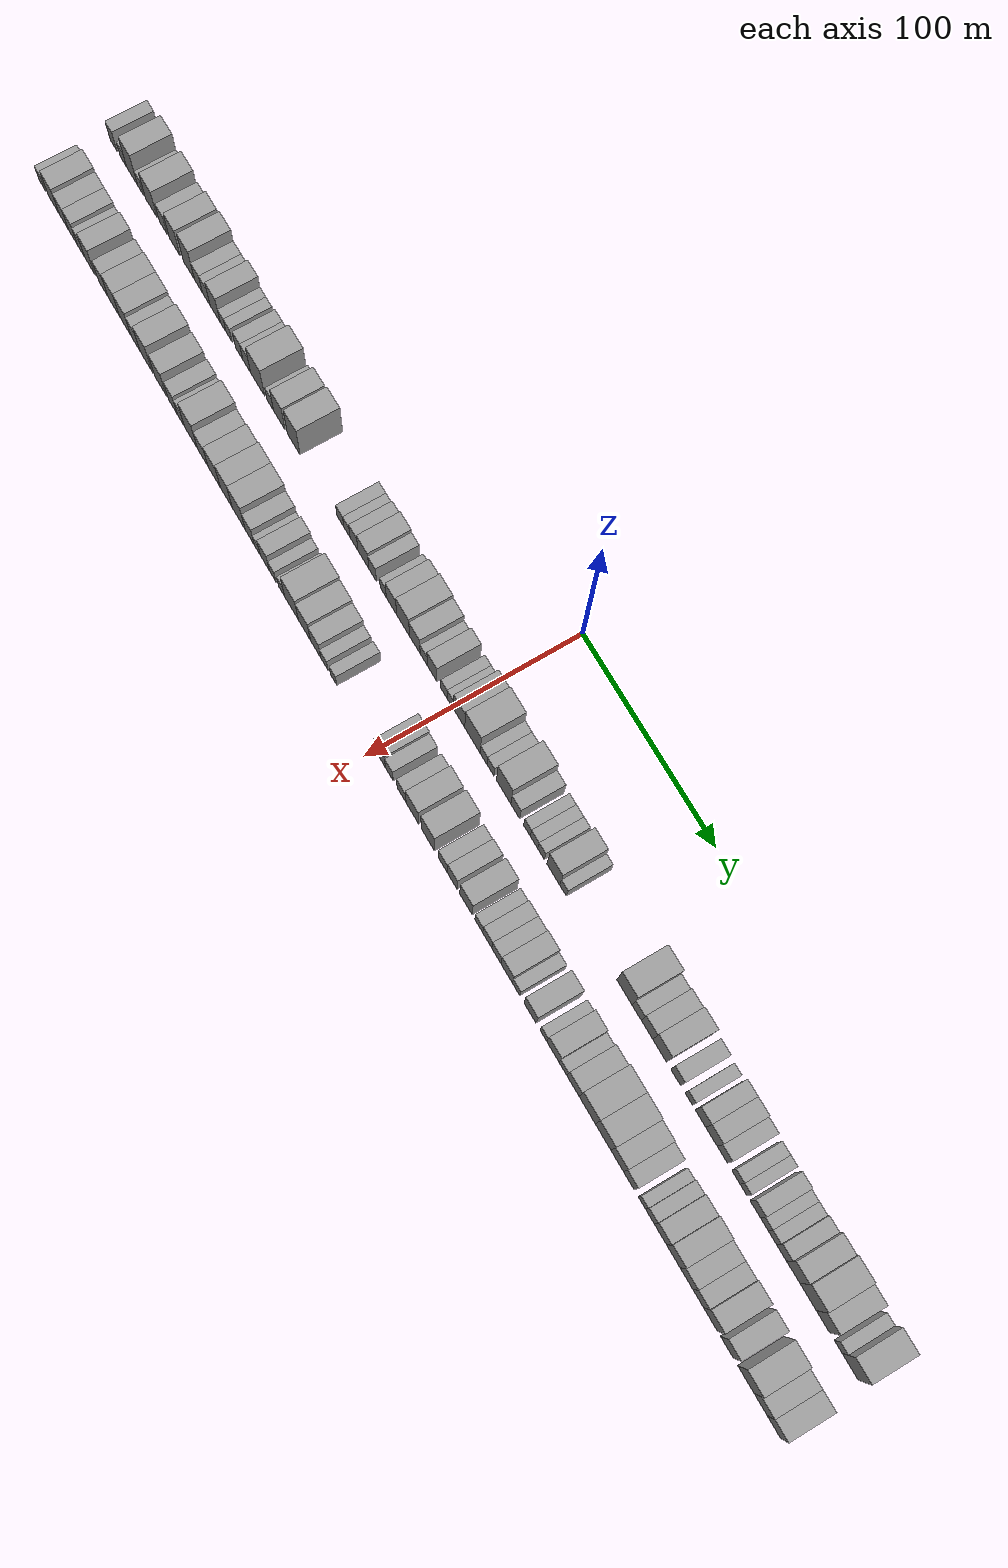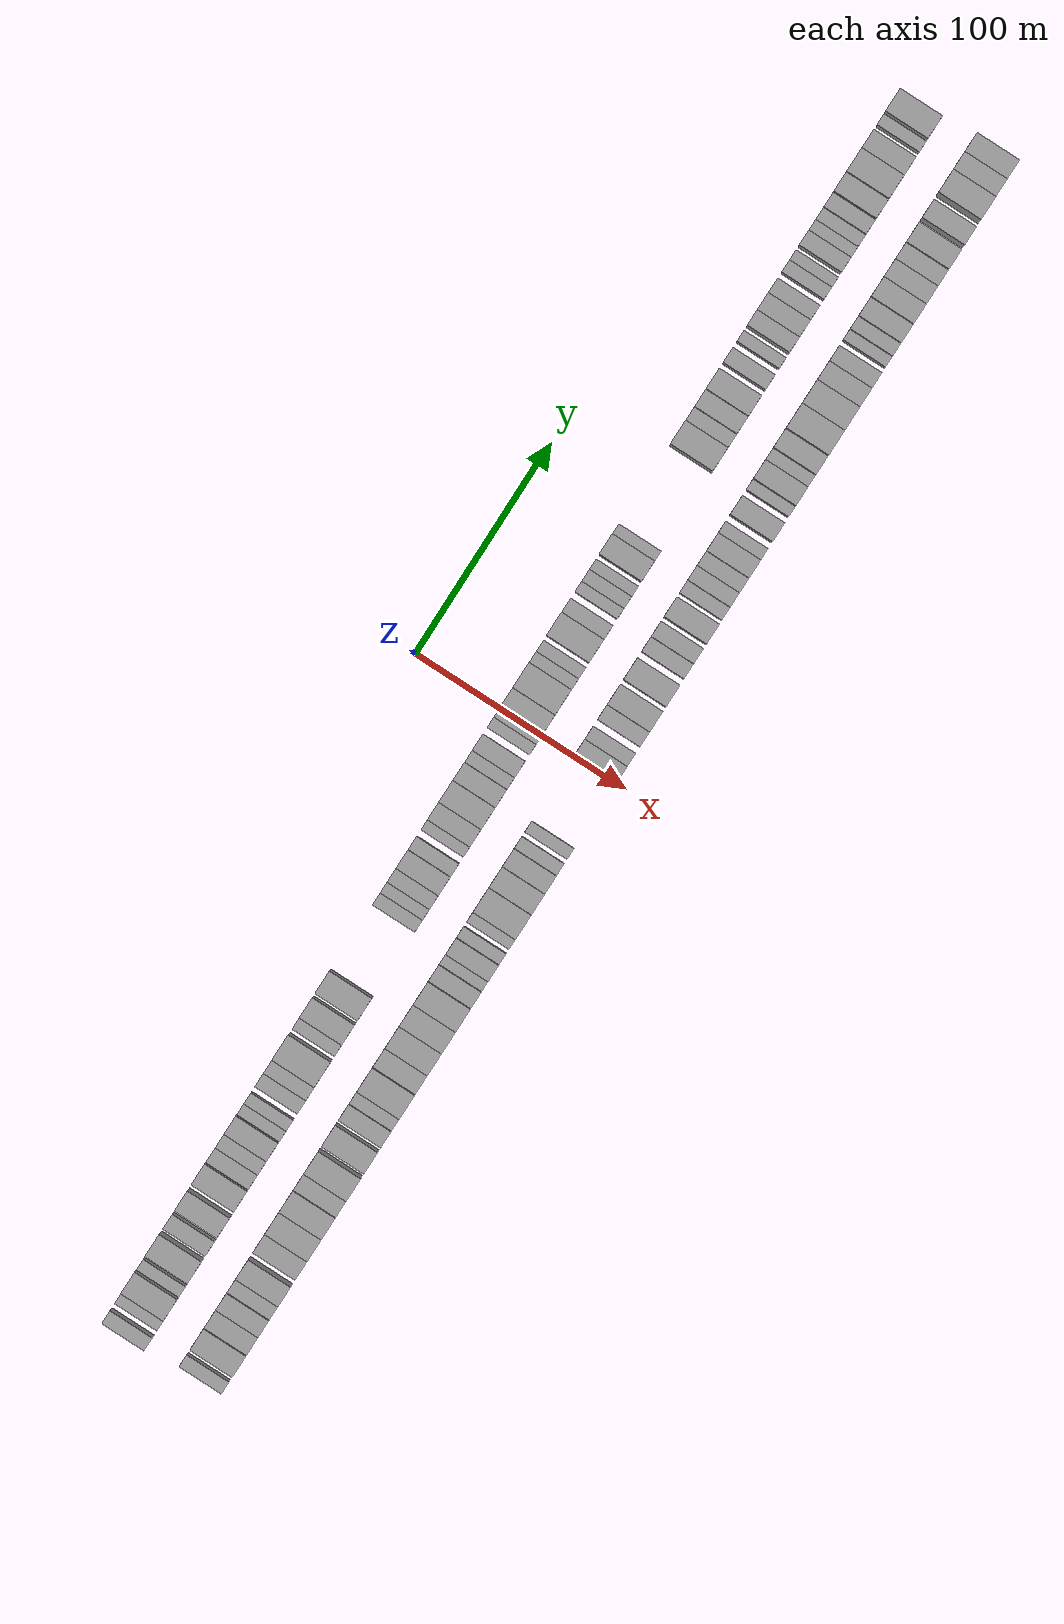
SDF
<sdf version="1.6">
 <world name="default">
  <scene>
   <sky><clouds><speed>12</speed></clouds></sky>
   <ambient>0.4 0.4 0.4 1</ambient>
   <background>0.7 0.7 0.7 1</background>
   <shadows>1</shadows>
  </scene>
  <gravity>0 0 -9.8066</gravity>
  <magnetic_field>6e-06 2.3e-05 -4.2e-05</magnetic_field>
  <physics default="0" name="default_physics" type="ode">
   <ode>
    <solver>
     <type>quick</type>
     <iters>10</iters>
     <sor>1.0</sor>
     <use_dynamic_moi_rescaling>0</use_dynamic_moi_rescaling>
    </solver>
    <constraints>
     <cfm>0</cfm>
     <erp>0.2</erp>
     <contact_max_correcting_vel>100</contact_max_correcting_vel>
     <contact_surface_layer>0.001</contact_surface_layer>
    </constraints>
   </ode>
   <max_step_size>0.004</max_step_size>
   <real_time_factor>1</real_time_factor>
   <real_time_update_rate>250</real_time_update_rate>
  </physics>
  <light name="sun" type="directional">
   <pose>0 0 10 0 0 0</pose>
   <diffuse>0.8 0.8 0.8 1</diffuse>
   <specular>0.2 0.2 0.2 1</specular>
   <attenuation>
    <range>1000</range>
    <constant>0.9</constant>
    <linear>0.01</linear>
    <quadratic>0.001</quadratic>
   </attenuation>
   <direction>-0.5 0.1 -0.9</direction>
  </light>
  <model name="building_1">
   <static>1</static>
   <pose>50.0000 -286.9524 0 0.000000 0.000000 0.000000</pose>
   <link name="link">
    <pose>0 0 7.50 0 0 0</pose>
    <collision name="collision"><geometry><box><size>20.0000 6.0952 15.0000</size></box></geometry></collision>
    <visual name="visual">
     <cast_shadows>0</cast_shadows>
     <geometry><box><size>20.0000 6.0952 15.0000</size></box></geometry>
     <material>
      <script>
       <uri>model://grey_wall/materials/scripts</uri>
       <uri>model://grey_wall/materials/textures</uri>
       <name>vrc/grey_wall</name>
      </script>
     </material>
    </visual>
   </link>
  </model>
  <model name="building_2">
   <static>1</static>
   <pose>50.0000 -278.0314 0 0.000000 0.000000 0.000000</pose>
   <link name="link">
    <pose>0 0 6.00 0 0 0</pose>
    <collision name="collision"><geometry><box><size>20.0000 5.7467 12.0000</size></box></geometry></collision>
    <visual name="visual">
     <cast_shadows>0</cast_shadows>
     <geometry><box><size>20.0000 5.7467 12.0000</size></box></geometry>
     <material>
      <script>
       <uri>model://grey_wall/materials/scripts</uri>
       <uri>model://grey_wall/materials/textures</uri>
       <name>vrc/grey_wall</name>
      </script>
     </material>
    </visual>
   </link>
  </model>
  <model name="building_3">
   <static>1</static>
   <pose>50.0000 -270.0946 0 0.000000 0.000000 0.000000</pose>
   <link name="link">
    <pose>0 0 12.00 0 0 0</pose>
    <collision name="collision"><geometry><box><size>20.0000 10.1269 24.0000</size></box></geometry></collision>
    <visual name="visual">
     <cast_shadows>0</cast_shadows>
     <geometry><box><size>20.0000 10.1269 24.0000</size></box></geometry>
     <material>
      <script>
       <uri>model://grey_wall/materials/scripts</uri>
       <uri>model://grey_wall/materials/textures</uri>
       <name>vrc/grey_wall</name>
      </script>
     </material>
    </visual>
   </link>
  </model>
  <model name="building_4">
   <static>1</static>
   <pose>50.0000 -262.5063 0 0.000000 0.000000 0.000000</pose>
   <link name="link">
    <pose>0 0 6.00 0 0 0</pose>
    <collision name="collision"><geometry><box><size>20.0000 5.0498 12.0000</size></box></geometry></collision>
    <visual name="visual">
     <cast_shadows>0</cast_shadows>
     <geometry><box><size>20.0000 5.0498 12.0000</size></box></geometry>
     <material>
      <script>
       <uri>model://grey_wall/materials/scripts</uri>
       <uri>model://grey_wall/materials/textures</uri>
       <name>vrc/grey_wall</name>
      </script>
     </material>
    </visual>
   </link>
  </model>
  <model name="building_5">
   <static>1</static>
   <pose>50.0000 -252.7505 0 0.000000 0.000000 0.000000</pose>
   <link name="link">
    <pose>0 0 10.50 0 0 0</pose>
    <collision name="collision"><geometry><box><size>20.0000 10.4617 21.0000</size></box></geometry></collision>
    <visual name="visual">
     <cast_shadows>0</cast_shadows>
     <geometry><box><size>20.0000 10.4617 21.0000</size></box></geometry>
     <material>
      <script>
       <uri>model://grey_wall/materials/scripts</uri>
       <uri>model://grey_wall/materials/textures</uri>
       <name>vrc/grey_wall</name>
      </script>
     </material>
    </visual>
   </link>
  </model>
  <model name="building_6">
   <static>1</static>
   <pose>50.0000 -242.0222 0 0.000000 0.000000 0.000000</pose>
   <link name="link">
    <pose>0 0 7.50 0 0 0</pose>
    <collision name="collision"><geometry><box><size>20.0000 6.9950 15.0000</size></box></geometry></collision>
    <visual name="visual">
     <cast_shadows>0</cast_shadows>
     <geometry><box><size>20.0000 6.9950 15.0000</size></box></geometry>
     <material>
      <script>
       <uri>model://grey_wall/materials/scripts</uri>
       <uri>model://grey_wall/materials/textures</uri>
       <name>vrc/grey_wall</name>
      </script>
     </material>
    </visual>
   </link>
  </model>
  <model name="building_7">
   <static>1</static>
   <pose>50.0000 -231.7771 0 0.000000 0.000000 0.000000</pose>
   <link name="link">
    <pose>0 0 10.50 0 0 0</pose>
    <collision name="collision"><geometry><box><size>20.0000 9.4951 21.0000</size></box></geometry></collision>
    <visual name="visual">
     <cast_shadows>0</cast_shadows>
     <geometry><box><size>20.0000 9.4951 21.0000</size></box></geometry>
     <material>
      <script>
       <uri>model://grey_wall/materials/scripts</uri>
       <uri>model://grey_wall/materials/textures</uri>
       <name>vrc/grey_wall</name>
      </script>
     </material>
    </visual>
   </link>
  </model>
  <model name="building_8">
   <static>1</static>
   <pose>50.0000 -219.0896 0 0.000000 0.000000 0.000000</pose>
   <link name="link">
    <pose>0 0 12.00 0 0 0</pose>
    <collision name="collision"><geometry><box><size>20.0000 9.8800 24.0000</size></box></geometry></collision>
    <visual name="visual">
     <cast_shadows>0</cast_shadows>
     <geometry><box><size>20.0000 9.8800 24.0000</size></box></geometry>
     <material>
      <script>
       <uri>model://grey_wall/materials/scripts</uri>
       <uri>model://grey_wall/materials/textures</uri>
       <name>vrc/grey_wall</name>
      </script>
     </material>
    </visual>
   </link>
  </model>
  <model name="building_9">
   <static>1</static>
   <pose>50.0000 -210.7066 0 0.000000 0.000000 0.000000</pose>
   <link name="link">
    <pose>0 0 7.50 0 0 0</pose>
    <collision name="collision"><geometry><box><size>20.0000 6.8859 15.0000</size></box></geometry></collision>
    <visual name="visual">
     <cast_shadows>0</cast_shadows>
     <geometry><box><size>20.0000 6.8859 15.0000</size></box></geometry>
     <material>
      <script>
       <uri>model://grey_wall/materials/scripts</uri>
       <uri>model://grey_wall/materials/textures</uri>
       <name>vrc/grey_wall</name>
      </script>
     </material>
    </visual>
   </link>
  </model>
  <model name="building_10">
   <static>1</static>
   <pose>50.0000 -203.8775 0 0.000000 0.000000 0.000000</pose>
   <link name="link">
    <pose>0 0 7.50 0 0 0</pose>
    <collision name="collision"><geometry><box><size>20.0000 6.7725 15.0000</size></box></geometry></collision>
    <visual name="visual">
     <cast_shadows>0</cast_shadows>
     <geometry><box><size>20.0000 6.7725 15.0000</size></box></geometry>
     <material>
      <script>
       <uri>model://grey_wall/materials/scripts</uri>
       <uri>model://grey_wall/materials/textures</uri>
       <name>vrc/grey_wall</name>
      </script>
     </material>
    </visual>
   </link>
  </model>
  <model name="building_11">
   <static>1</static>
   <pose>50.0000 -196.1210 0 0.000000 0.000000 0.000000</pose>
   <link name="link">
    <pose>0 0 10.50 0 0 0</pose>
    <collision name="collision"><geometry><box><size>20.0000 8.7404 21.0000</size></box></geometry></collision>
    <visual name="visual">
     <cast_shadows>0</cast_shadows>
     <geometry><box><size>20.0000 8.7404 21.0000</size></box></geometry>
     <material>
      <script>
       <uri>model://grey_wall/materials/scripts</uri>
       <uri>model://grey_wall/materials/textures</uri>
       <name>vrc/grey_wall</name>
      </script>
     </material>
    </visual>
   </link>
  </model>
  <model name="building_12">
   <static>1</static>
   <pose>50.0000 -189.2154 0 0.000000 0.000000 0.000000</pose>
   <link name="link">
    <pose>0 0 6.00 0 0 0</pose>
    <collision name="collision"><geometry><box><size>20.0000 5.0708 12.0000</size></box></geometry></collision>
    <visual name="visual">
     <cast_shadows>0</cast_shadows>
     <geometry><box><size>20.0000 5.0708 12.0000</size></box></geometry>
     <material>
      <script>
       <uri>model://grey_wall/materials/scripts</uri>
       <uri>model://grey_wall/materials/textures</uri>
       <name>vrc/grey_wall</name>
      </script>
     </material>
    </visual>
   </link>
  </model>
  <model name="building_13">
   <static>1</static>
   <pose>50.0000 -184.0601 0 0.000000 0.000000 0.000000</pose>
   <link name="link">
    <pose>0 0 6.00 0 0 0</pose>
    <collision name="collision"><geometry><box><size>20.0000 5.2398 12.0000</size></box></geometry></collision>
    <visual name="visual">
     <cast_shadows>0</cast_shadows>
     <geometry><box><size>20.0000 5.2398 12.0000</size></box></geometry>
     <material>
      <script>
       <uri>model://grey_wall/materials/scripts</uri>
       <uri>model://grey_wall/materials/textures</uri>
       <name>vrc/grey_wall</name>
      </script>
     </material>
    </visual>
   </link>
  </model>
  <model name="building_14">
   <static>1</static>
   <pose>50.0000 -175.2972 0 0.000000 0.000000 0.000000</pose>
   <link name="link">
    <pose>0 0 7.50 0 0 0</pose>
    <collision name="collision"><geometry><box><size>20.0000 6.2859 15.0000</size></box></geometry></collision>
    <visual name="visual">
     <cast_shadows>0</cast_shadows>
     <geometry><box><size>20.0000 6.2859 15.0000</size></box></geometry>
     <material>
      <script>
       <uri>model://grey_wall/materials/scripts</uri>
       <uri>model://grey_wall/materials/textures</uri>
       <name>vrc/grey_wall</name>
      </script>
     </material>
    </visual>
   </link>
  </model>
  <model name="building_15">
   <static>1</static>
   <pose>50.0000 -168.8099 0 0.000000 0.000000 0.000000</pose>
   <link name="link">
    <pose>0 0 7.50 0 0 0</pose>
    <collision name="collision"><geometry><box><size>20.0000 6.6888 15.0000</size></box></geometry></collision>
    <visual name="visual">
     <cast_shadows>0</cast_shadows>
     <geometry><box><size>20.0000 6.6888 15.0000</size></box></geometry>
     <material>
      <script>
       <uri>model://grey_wall/materials/scripts</uri>
       <uri>model://grey_wall/materials/textures</uri>
       <name>vrc/grey_wall</name>
      </script>
     </material>
    </visual>
   </link>
  </model>
  <model name="building_16">
   <static>1</static>
   <pose>50.0000 -159.4696 0 0.000000 0.000000 0.000000</pose>
   <link name="link">
    <pose>0 0 12.00 0 0 0</pose>
    <collision name="collision"><geometry><box><size>20.0000 11.9917 24.0000</size></box></geometry></collision>
    <visual name="visual">
     <cast_shadows>0</cast_shadows>
     <geometry><box><size>20.0000 11.9917 24.0000</size></box></geometry>
     <material>
      <script>
       <uri>model://grey_wall/materials/scripts</uri>
       <uri>model://grey_wall/materials/textures</uri>
       <name>vrc/grey_wall</name>
      </script>
     </material>
    </visual>
   </link>
  </model>
  <model name="building_17">
   <static>1</static>
   <pose>50.0000 -148.5982 0 0.000000 0.000000 0.000000</pose>
   <link name="link">
    <pose>0 0 6.00 0 0 0</pose>
    <collision name="collision"><geometry><box><size>20.0000 5.7511 12.0000</size></box></geometry></collision>
    <visual name="visual">
     <cast_shadows>0</cast_shadows>
     <geometry><box><size>20.0000 5.7511 12.0000</size></box></geometry>
     <material>
      <script>
       <uri>model://grey_wall/materials/scripts</uri>
       <uri>model://grey_wall/materials/textures</uri>
       <name>vrc/grey_wall</name>
      </script>
     </material>
    </visual>
   </link>
  </model>
  <model name="building_18">
   <static>1</static>
   <pose>50.0000 -140.9373 0 0.000000 0.000000 0.000000</pose>
   <link name="link">
    <pose>0 0 10.50 0 0 0</pose>
    <collision name="collision"><geometry><box><size>20.0000 9.5707 21.0000</size></box></geometry></collision>
    <visual name="visual">
     <cast_shadows>0</cast_shadows>
     <geometry><box><size>20.0000 9.5707 21.0000</size></box></geometry>
     <material>
      <script>
       <uri>model://grey_wall/materials/scripts</uri>
       <uri>model://grey_wall/materials/textures</uri>
       <name>vrc/grey_wall</name>
      </script>
     </material>
    </visual>
   </link>
  </model>
  <model name="building_19">
   <static>1</static>
   <pose>50.0000 -128.8325 0 0.000000 0.000000 0.000000</pose>
   <link name="link">
    <pose>0 0 12.00 0 0 0</pose>
    <collision name="collision"><geometry><box><size>20.0000 10.6388 24.0000</size></box></geometry></collision>
    <visual name="visual">
     <cast_shadows>0</cast_shadows>
     <geometry><box><size>20.0000 10.6388 24.0000</size></box></geometry>
     <material>
      <script>
       <uri>model://grey_wall/materials/scripts</uri>
       <uri>model://grey_wall/materials/textures</uri>
       <name>vrc/grey_wall</name>
      </script>
     </material>
    </visual>
   </link>
  </model>
  <model name="building_20">
   <static>1</static>
   <pose>50.0000 -89.9848 0 0.000000 0.000000 0.000000</pose>
   <link name="link">
    <pose>0 0 6.00 0 0 0</pose>
    <collision name="collision"><geometry><box><size>20.0000 5.6855 12.0000</size></box></geometry></collision>
    <visual name="visual">
     <cast_shadows>0</cast_shadows>
     <geometry><box><size>20.0000 5.6855 12.0000</size></box></geometry>
     <material>
      <script>
       <uri>model://grey_wall/materials/scripts</uri>
       <uri>model://grey_wall/materials/textures</uri>
       <name>vrc/grey_wall</name>
      </script>
     </material>
    </visual>
   </link>
  </model>
  <model name="building_21">
   <static>1</static>
   <pose>50.0000 -84.5897 0 0.000000 0.000000 0.000000</pose>
   <link name="link">
    <pose>0 0 6.00 0 0 0</pose>
    <collision name="collision"><geometry><box><size>20.0000 5.1047 12.0000</size></box></geometry></collision>
    <visual name="visual">
     <cast_shadows>0</cast_shadows>
     <geometry><box><size>20.0000 5.1047 12.0000</size></box></geometry>
     <material>
      <script>
       <uri>model://grey_wall/materials/scripts</uri>
       <uri>model://grey_wall/materials/textures</uri>
       <name>vrc/grey_wall</name>
      </script>
     </material>
    </visual>
   </link>
  </model>
  <model name="building_22">
   <static>1</static>
   <pose>50.0000 -78.7702 0 0.000000 0.000000 0.000000</pose>
   <link name="link">
    <pose>0 0 7.50 0 0 0</pose>
    <collision name="collision"><geometry><box><size>20.0000 6.5341 15.0000</size></box></geometry></collision>
    <visual name="visual">
     <cast_shadows>0</cast_shadows>
     <geometry><box><size>20.0000 6.5341 15.0000</size></box></geometry>
     <material>
      <script>
       <uri>model://grey_wall/materials/scripts</uri>
       <uri>model://grey_wall/materials/textures</uri>
       <name>vrc/grey_wall</name>
      </script>
     </material>
    </visual>
   </link>
  </model>
  <model name="building_23">
   <static>1</static>
   <pose>50.0000 -71.0787 0 0.000000 0.000000 0.000000</pose>
   <link name="link">
    <pose>0 0 9.00 0 0 0</pose>
    <collision name="collision"><geometry><box><size>20.0000 8.8489 18.0000</size></box></geometry></collision>
    <visual name="visual">
     <cast_shadows>0</cast_shadows>
     <geometry><box><size>20.0000 8.8489 18.0000</size></box></geometry>
     <material>
      <script>
       <uri>model://grey_wall/materials/scripts</uri>
       <uri>model://grey_wall/materials/textures</uri>
       <name>vrc/grey_wall</name>
      </script>
     </material>
    </visual>
   </link>
  </model>
  <model name="building_24">
   <static>1</static>
   <pose>50.0000 -63.5468 0 0.000000 0.000000 0.000000</pose>
   <link name="link">
    <pose>0 0 7.50 0 0 0</pose>
    <collision name="collision"><geometry><box><size>20.0000 6.2149 15.0000</size></box></geometry></collision>
    <visual name="visual">
     <cast_shadows>0</cast_shadows>
     <geometry><box><size>20.0000 6.2149 15.0000</size></box></geometry>
     <material>
      <script>
       <uri>model://grey_wall/materials/scripts</uri>
       <uri>model://grey_wall/materials/textures</uri>
       <name>vrc/grey_wall</name>
      </script>
     </material>
    </visual>
   </link>
  </model>
  <model name="building_25">
   <static>1</static>
   <pose>50.0000 -55.0133 0 0.000000 0.000000 0.000000</pose>
   <link name="link">
    <pose>0 0 6.00 0 0 0</pose>
    <collision name="collision"><geometry><box><size>20.0000 4.8523 12.0000</size></box></geometry></collision>
    <visual name="visual">
     <cast_shadows>0</cast_shadows>
     <geometry><box><size>20.0000 4.8523 12.0000</size></box></geometry>
     <material>
      <script>
       <uri>model://grey_wall/materials/scripts</uri>
       <uri>model://grey_wall/materials/textures</uri>
       <name>vrc/grey_wall</name>
      </script>
     </material>
    </visual>
   </link>
  </model>
  <model name="building_26">
   <static>1</static>
   <pose>50.0000 -48.4368 0 0.000000 0.000000 0.000000</pose>
   <link name="link">
    <pose>0 0 9.00 0 0 0</pose>
    <collision name="collision"><geometry><box><size>20.0000 8.3007 18.0000</size></box></geometry></collision>
    <visual name="visual">
     <cast_shadows>0</cast_shadows>
     <geometry><box><size>20.0000 8.3007 18.0000</size></box></geometry>
     <material>
      <script>
       <uri>model://grey_wall/materials/scripts</uri>
       <uri>model://grey_wall/materials/textures</uri>
       <name>vrc/grey_wall</name>
      </script>
     </material>
    </visual>
   </link>
  </model>
  <model name="building_27">
   <static>1</static>
   <pose>50.0000 -39.1435 0 0.000000 0.000000 0.000000</pose>
   <link name="link">
    <pose>0 0 10.50 0 0 0</pose>
    <collision name="collision"><geometry><box><size>20.0000 10.2858 21.0000</size></box></geometry></collision>
    <visual name="visual">
     <cast_shadows>0</cast_shadows>
     <geometry><box><size>20.0000 10.2858 21.0000</size></box></geometry>
     <material>
      <script>
       <uri>model://grey_wall/materials/scripts</uri>
       <uri>model://grey_wall/materials/textures</uri>
       <name>vrc/grey_wall</name>
      </script>
     </material>
    </visual>
   </link>
  </model>
  <model name="building_28">
   <static>1</static>
   <pose>50.0000 -29.7491 0 0.000000 0.000000 0.000000</pose>
   <link name="link">
    <pose>0 0 9.00 0 0 0</pose>
    <collision name="collision"><geometry><box><size>20.0000 8.5032 18.0000</size></box></geometry></collision>
    <visual name="visual">
     <cast_shadows>0</cast_shadows>
     <geometry><box><size>20.0000 8.5032 18.0000</size></box></geometry>
     <material>
      <script>
       <uri>model://grey_wall/materials/scripts</uri>
       <uri>model://grey_wall/materials/textures</uri>
       <name>vrc/grey_wall</name>
      </script>
     </material>
    </visual>
   </link>
  </model>
  <model name="building_29">
   <static>1</static>
   <pose>50.0000 -22.7021 0 0.000000 0.000000 0.000000</pose>
   <link name="link">
    <pose>0 0 6.00 0 0 0</pose>
    <collision name="collision"><geometry><box><size>20.0000 5.5906 12.0000</size></box></geometry></collision>
    <visual name="visual">
     <cast_shadows>0</cast_shadows>
     <geometry><box><size>20.0000 5.5906 12.0000</size></box></geometry>
     <material>
      <script>
       <uri>model://grey_wall/materials/scripts</uri>
       <uri>model://grey_wall/materials/textures</uri>
       <name>vrc/grey_wall</name>
      </script>
     </material>
    </visual>
   </link>
  </model>
  <model name="building_30">
   <static>1</static>
   <pose>50.0000 -16.0289 0 0.000000 0.000000 0.000000</pose>
   <link name="link">
    <pose>0 0 9.00 0 0 0</pose>
    <collision name="collision"><geometry><box><size>20.0000 7.7559 18.0000</size></box></geometry></collision>
    <visual name="visual">
     <cast_shadows>0</cast_shadows>
     <geometry><box><size>20.0000 7.7559 18.0000</size></box></geometry>
     <material>
      <script>
       <uri>model://grey_wall/materials/scripts</uri>
       <uri>model://grey_wall/materials/textures</uri>
       <name>vrc/grey_wall</name>
      </script>
     </material>
    </visual>
   </link>
  </model>
  <model name="building_31">
   <static>1</static>
   <pose>50.0000 -6.6972 0 0.000000 0.000000 0.000000</pose>
   <link name="link">
    <pose>0 0 6.00 0 0 0</pose>
    <collision name="collision"><geometry><box><size>20.0000 4.9074 12.0000</size></box></geometry></collision>
    <visual name="visual">
     <cast_shadows>0</cast_shadows>
     <geometry><box><size>20.0000 4.9074 12.0000</size></box></geometry>
     <material>
      <script>
       <uri>model://grey_wall/materials/scripts</uri>
       <uri>model://grey_wall/materials/textures</uri>
       <name>vrc/grey_wall</name>
      </script>
     </material>
    </visual>
   </link>
  </model>
  <model name="building_32">
   <static>1</static>
   <pose>50.0000 -1.6938 0 0.000000 0.000000 0.000000</pose>
   <link name="link">
    <pose>0 0 6.00 0 0 0</pose>
    <collision name="collision"><geometry><box><size>20.0000 5.0994 12.0000</size></box></geometry></collision>
    <visual name="visual">
     <cast_shadows>0</cast_shadows>
     <geometry><box><size>20.0000 5.0994 12.0000</size></box></geometry>
     <material>
      <script>
       <uri>model://grey_wall/materials/scripts</uri>
       <uri>model://grey_wall/materials/textures</uri>
       <name>vrc/grey_wall</name>
      </script>
     </material>
    </visual>
   </link>
  </model>
  <model name="building_33">
   <static>1</static>
   <pose>50.0000 5.2274 0 0.000000 0.000000 0.000000</pose>
   <link name="link">
    <pose>0 0 10.50 0 0 0</pose>
    <collision name="collision"><geometry><box><size>20.0000 8.7430 21.0000</size></box></geometry></collision>
    <visual name="visual">
     <cast_shadows>0</cast_shadows>
     <geometry><box><size>20.0000 8.7430 21.0000</size></box></geometry>
     <material>
      <script>
       <uri>model://grey_wall/materials/scripts</uri>
       <uri>model://grey_wall/materials/textures</uri>
       <name>vrc/grey_wall</name>
      </script>
     </material>
    </visual>
   </link>
  </model>
  <model name="building_34">
   <static>1</static>
   <pose>50.0000 15.5698 0 0.000000 0.000000 0.000000</pose>
   <link name="link">
    <pose>0 0 12.00 0 0 0</pose>
    <collision name="collision"><geometry><box><size>20.0000 11.9417 24.0000</size></box></geometry></collision>
    <visual name="visual">
     <cast_shadows>0</cast_shadows>
     <geometry><box><size>20.0000 11.9417 24.0000</size></box></geometry>
     <material>
      <script>
       <uri>model://grey_wall/materials/scripts</uri>
       <uri>model://grey_wall/materials/textures</uri>
       <name>vrc/grey_wall</name>
      </script>
     </material>
    </visual>
   </link>
  </model>
  <model name="building_35">
   <static>1</static>
   <pose>50.0000 24.1677 0 0.000000 0.000000 0.000000</pose>
   <link name="link">
    <pose>0 0 6.00 0 0 0</pose>
    <collision name="collision"><geometry><box><size>20.0000 5.2542 12.0000</size></box></geometry></collision>
    <visual name="visual">
     <cast_shadows>0</cast_shadows>
     <geometry><box><size>20.0000 5.2542 12.0000</size></box></geometry>
     <material>
      <script>
       <uri>model://grey_wall/materials/scripts</uri>
       <uri>model://grey_wall/materials/textures</uri>
       <name>vrc/grey_wall</name>
      </script>
     </material>
    </visual>
   </link>
  </model>
  <model name="building_36">
   <static>1</static>
   <pose>50.0000 29.4664 0 0.000000 0.000000 0.000000</pose>
   <link name="link">
    <pose>0 0 6.00 0 0 0</pose>
    <collision name="collision"><geometry><box><size>20.0000 5.3432 12.0000</size></box></geometry></collision>
    <visual name="visual">
     <cast_shadows>0</cast_shadows>
     <geometry><box><size>20.0000 5.3432 12.0000</size></box></geometry>
     <material>
      <script>
       <uri>model://grey_wall/materials/scripts</uri>
       <uri>model://grey_wall/materials/textures</uri>
       <name>vrc/grey_wall</name>
      </script>
     </material>
    </visual>
   </link>
  </model>
  <model name="building_37">
   <static>1</static>
   <pose>50.0000 39.6358 0 0.000000 0.000000 0.000000</pose>
   <link name="link">
    <pose>0 0 12.00 0 0 0</pose>
    <collision name="collision"><geometry><box><size>20.0000 10.9956 24.0000</size></box></geometry></collision>
    <visual name="visual">
     <cast_shadows>0</cast_shadows>
     <geometry><box><size>20.0000 10.9956 24.0000</size></box></geometry>
     <material>
      <script>
       <uri>model://grey_wall/materials/scripts</uri>
       <uri>model://grey_wall/materials/textures</uri>
       <name>vrc/grey_wall</name>
      </script>
     </material>
    </visual>
   </link>
  </model>
  <model name="building_38">
   <static>1</static>
   <pose>50.0000 48.5020 0 0.000000 0.000000 0.000000</pose>
   <link name="link">
    <pose>0 0 7.50 0 0 0</pose>
    <collision name="collision"><geometry><box><size>20.0000 6.7369 15.0000</size></box></geometry></collision>
    <visual name="visual">
     <cast_shadows>0</cast_shadows>
     <geometry><box><size>20.0000 6.7369 15.0000</size></box></geometry>
     <material>
      <script>
       <uri>model://grey_wall/materials/scripts</uri>
       <uri>model://grey_wall/materials/textures</uri>
       <name>vrc/grey_wall</name>
      </script>
     </material>
    </visual>
   </link>
  </model>
  <model name="building_39">
   <static>1</static>
   <pose>50.0000 57.3776 0 0.000000 0.000000 0.000000</pose>
   <link name="link">
    <pose>0 0 6.00 0 0 0</pose>
    <collision name="collision"><geometry><box><size>20.0000 5.0143 12.0000</size></box></geometry></collision>
    <visual name="visual">
     <cast_shadows>0</cast_shadows>
     <geometry><box><size>20.0000 5.0143 12.0000</size></box></geometry>
     <material>
      <script>
       <uri>model://grey_wall/materials/scripts</uri>
       <uri>model://grey_wall/materials/textures</uri>
       <name>vrc/grey_wall</name>
      </script>
     </material>
    </visual>
   </link>
  </model>
  <model name="building_40">
   <static>1</static>
   <pose>50.0000 62.7065 0 0.000000 0.000000 0.000000</pose>
   <link name="link">
    <pose>0 0 6.00 0 0 0</pose>
    <collision name="collision"><geometry><box><size>20.0000 5.6437 12.0000</size></box></geometry></collision>
    <visual name="visual">
     <cast_shadows>0</cast_shadows>
     <geometry><box><size>20.0000 5.6437 12.0000</size></box></geometry>
     <material>
      <script>
       <uri>model://grey_wall/materials/scripts</uri>
       <uri>model://grey_wall/materials/textures</uri>
       <name>vrc/grey_wall</name>
      </script>
     </material>
    </visual>
   </link>
  </model>
  <model name="building_41">
   <static>1</static>
   <pose>50.0000 67.9762 0 0.000000 0.000000 0.000000</pose>
   <link name="link">
    <pose>0 0 6.00 0 0 0</pose>
    <collision name="collision"><geometry><box><size>20.0000 4.8956 12.0000</size></box></geometry></collision>
    <visual name="visual">
     <cast_shadows>0</cast_shadows>
     <geometry><box><size>20.0000 4.8956 12.0000</size></box></geometry>
     <material>
      <script>
       <uri>model://grey_wall/materials/scripts</uri>
       <uri>model://grey_wall/materials/textures</uri>
       <name>vrc/grey_wall</name>
      </script>
     </material>
    </visual>
   </link>
  </model>
  <model name="building_42">
   <static>1</static>
   <pose>50.0000 77.2399 0 0.000000 0.000000 0.000000</pose>
   <link name="link">
    <pose>0 0 10.50 0 0 0</pose>
    <collision name="collision"><geometry><box><size>20.0000 9.6318 21.0000</size></box></geometry></collision>
    <visual name="visual">
     <cast_shadows>0</cast_shadows>
     <geometry><box><size>20.0000 9.6318 21.0000</size></box></geometry>
     <material>
      <script>
       <uri>model://grey_wall/materials/scripts</uri>
       <uri>model://grey_wall/materials/textures</uri>
       <name>vrc/grey_wall</name>
      </script>
     </material>
    </visual>
   </link>
  </model>
  <model name="building_43">
   <static>1</static>
   <pose>50.0000 84.5224 0 0.000000 0.000000 0.000000</pose>
   <link name="link">
    <pose>0 0 6.00 0 0 0</pose>
    <collision name="collision"><geometry><box><size>20.0000 4.9331 12.0000</size></box></geometry></collision>
    <visual name="visual">
     <cast_shadows>0</cast_shadows>
     <geometry><box><size>20.0000 4.9331 12.0000</size></box></geometry>
     <material>
      <script>
       <uri>model://grey_wall/materials/scripts</uri>
       <uri>model://grey_wall/materials/textures</uri>
       <name>vrc/grey_wall</name>
      </script>
     </material>
    </visual>
   </link>
  </model>
  <model name="building_44">
   <static>1</static>
   <pose>50.0000 129.7058 0 0.000000 0.000000 0.000000</pose>
   <link name="link">
    <pose>0 0 12.00 0 0 0</pose>
    <collision name="collision"><geometry><box><size>20.0000 11.1446 24.0000</size></box></geometry></collision>
    <visual name="visual">
     <cast_shadows>0</cast_shadows>
     <geometry><box><size>20.0000 11.1446 24.0000</size></box></geometry>
     <material>
      <script>
       <uri>model://grey_wall/materials/scripts</uri>
       <uri>model://grey_wall/materials/textures</uri>
       <name>vrc/grey_wall</name>
      </script>
     </material>
    </visual>
   </link>
  </model>
  <model name="building_45">
   <static>1</static>
   <pose>50.0000 138.6264 0 0.000000 0.000000 0.000000</pose>
   <link name="link">
    <pose>0 0 7.50 0 0 0</pose>
    <collision name="collision"><geometry><box><size>20.0000 6.6966 15.0000</size></box></geometry></collision>
    <visual name="visual">
     <cast_shadows>0</cast_shadows>
     <geometry><box><size>20.0000 6.6966 15.0000</size></box></geometry>
     <material>
      <script>
       <uri>model://grey_wall/materials/scripts</uri>
       <uri>model://grey_wall/materials/textures</uri>
       <name>vrc/grey_wall</name>
      </script>
     </material>
    </visual>
   </link>
  </model>
  <model name="building_46">
   <static>1</static>
   <pose>50.0000 146.0782 0 0.000000 0.000000 0.000000</pose>
   <link name="link">
    <pose>0 0 9.00 0 0 0</pose>
    <collision name="collision"><geometry><box><size>20.0000 8.2069 18.0000</size></box></geometry></collision>
    <visual name="visual">
     <cast_shadows>0</cast_shadows>
     <geometry><box><size>20.0000 8.2069 18.0000</size></box></geometry>
     <material>
      <script>
       <uri>model://grey_wall/materials/scripts</uri>
       <uri>model://grey_wall/materials/textures</uri>
       <name>vrc/grey_wall</name>
      </script>
     </material>
    </visual>
   </link>
  </model>
  <model name="building_47">
   <static>1</static>
   <pose>50.0000 155.0491 0 0.000000 0.000000 0.000000</pose>
   <link name="link">
    <pose>0 0 10.50 0 0 0</pose>
    <collision name="collision"><geometry><box><size>20.0000 9.7350 21.0000</size></box></geometry></collision>
    <visual name="visual">
     <cast_shadows>0</cast_shadows>
     <geometry><box><size>20.0000 9.7350 21.0000</size></box></geometry>
     <material>
      <script>
       <uri>model://grey_wall/materials/scripts</uri>
       <uri>model://grey_wall/materials/textures</uri>
       <name>vrc/grey_wall</name>
      </script>
     </material>
    </visual>
   </link>
  </model>
  <model name="building_48">
   <static>1</static>
   <pose>50.0000 166.4824 0 0.000000 0.000000 0.000000</pose>
   <link name="link">
    <pose>0 0 7.50 0 0 0</pose>
    <collision name="collision"><geometry><box><size>20.0000 7.1317 15.0000</size></box></geometry></collision>
    <visual name="visual">
     <cast_shadows>0</cast_shadows>
     <geometry><box><size>20.0000 7.1317 15.0000</size></box></geometry>
     <material>
      <script>
       <uri>model://grey_wall/materials/scripts</uri>
       <uri>model://grey_wall/materials/textures</uri>
       <name>vrc/grey_wall</name>
      </script>
     </material>
    </visual>
   </link>
  </model>
  <model name="building_49">
   <static>1</static>
   <pose>50.0000 175.6616 0 0.000000 0.000000 0.000000</pose>
   <link name="link">
    <pose>0 0 6.00 0 0 0</pose>
    <collision name="collision"><geometry><box><size>20.0000 5.2266 12.0000</size></box></geometry></collision>
    <visual name="visual">
     <cast_shadows>0</cast_shadows>
     <geometry><box><size>20.0000 5.2266 12.0000</size></box></geometry>
     <material>
      <script>
       <uri>model://grey_wall/materials/scripts</uri>
       <uri>model://grey_wall/materials/textures</uri>
       <name>vrc/grey_wall</name>
      </script>
     </material>
    </visual>
   </link>
  </model>
  <model name="building_50">
   <static>1</static>
   <pose>50.0000 183.9300 0 0.000000 0.000000 0.000000</pose>
   <link name="link">
    <pose>0 0 9.00 0 0 0</pose>
    <collision name="collision"><geometry><box><size>20.0000 7.3103 18.0000</size></box></geometry></collision>
    <visual name="visual">
     <cast_shadows>0</cast_shadows>
     <geometry><box><size>20.0000 7.3103 18.0000</size></box></geometry>
     <material>
      <script>
       <uri>model://grey_wall/materials/scripts</uri>
       <uri>model://grey_wall/materials/textures</uri>
       <name>vrc/grey_wall</name>
      </script>
     </material>
    </visual>
   </link>
  </model>
  <model name="building_51">
   <static>1</static>
   <pose>50.0000 191.6336 0 0.000000 0.000000 0.000000</pose>
   <link name="link">
    <pose>0 0 9.00 0 0 0</pose>
    <collision name="collision"><geometry><box><size>20.0000 8.0969 18.0000</size></box></geometry></collision>
    <visual name="visual">
     <cast_shadows>0</cast_shadows>
     <geometry><box><size>20.0000 8.0969 18.0000</size></box></geometry>
     <material>
      <script>
       <uri>model://grey_wall/materials/scripts</uri>
       <uri>model://grey_wall/materials/textures</uri>
       <name>vrc/grey_wall</name>
      </script>
     </material>
    </visual>
   </link>
  </model>
  <model name="building_52">
   <static>1</static>
   <pose>50.0000 199.2062 0 0.000000 0.000000 0.000000</pose>
   <link name="link">
    <pose>0 0 7.50 0 0 0</pose>
    <collision name="collision"><geometry><box><size>20.0000 7.0482 15.0000</size></box></geometry></collision>
    <visual name="visual">
     <cast_shadows>0</cast_shadows>
     <geometry><box><size>20.0000 7.0482 15.0000</size></box></geometry>
     <material>
      <script>
       <uri>model://grey_wall/materials/scripts</uri>
       <uri>model://grey_wall/materials/textures</uri>
       <name>vrc/grey_wall</name>
      </script>
     </material>
    </visual>
   </link>
  </model>
  <model name="building_53">
   <static>1</static>
   <pose>50.0000 208.6064 0 0.000000 0.000000 0.000000</pose>
   <link name="link">
    <pose>0 0 6.00 0 0 0</pose>
    <collision name="collision"><geometry><box><size>20.0000 5.7521 12.0000</size></box></geometry></collision>
    <visual name="visual">
     <cast_shadows>0</cast_shadows>
     <geometry><box><size>20.0000 5.7521 12.0000</size></box></geometry>
     <material>
      <script>
       <uri>model://grey_wall/materials/scripts</uri>
       <uri>model://grey_wall/materials/textures</uri>
       <name>vrc/grey_wall</name>
      </script>
     </material>
    </visual>
   </link>
  </model>
  <model name="building_54">
   <static>1</static>
   <pose>50.0000 213.8848 0 0.000000 0.000000 0.000000</pose>
   <link name="link">
    <pose>0 0 6.00 0 0 0</pose>
    <collision name="collision"><geometry><box><size>20.0000 4.8046 12.0000</size></box></geometry></collision>
    <visual name="visual">
     <cast_shadows>0</cast_shadows>
     <geometry><box><size>20.0000 4.8046 12.0000</size></box></geometry>
     <material>
      <script>
       <uri>model://grey_wall/materials/scripts</uri>
       <uri>model://grey_wall/materials/textures</uri>
       <name>vrc/grey_wall</name>
      </script>
     </material>
    </visual>
   </link>
  </model>
  <model name="building_55">
   <static>1</static>
   <pose>50.0000 221.8105 0 0.000000 0.000000 0.000000</pose>
   <link name="link">
    <pose>0 0 7.50 0 0 0</pose>
    <collision name="collision"><geometry><box><size>20.0000 7.0468 15.0000</size></box></geometry></collision>
    <visual name="visual">
     <cast_shadows>0</cast_shadows>
     <geometry><box><size>20.0000 7.0468 15.0000</size></box></geometry>
     <material>
      <script>
       <uri>model://grey_wall/materials/scripts</uri>
       <uri>model://grey_wall/materials/textures</uri>
       <name>vrc/grey_wall</name>
      </script>
     </material>
    </visual>
   </link>
  </model>
  <model name="building_56">
   <static>1</static>
   <pose>50.0000 227.9521 0 0.000000 0.000000 0.000000</pose>
   <link name="link">
    <pose>0 0 6.00 0 0 0</pose>
    <collision name="collision"><geometry><box><size>20.0000 5.2365 12.0000</size></box></geometry></collision>
    <visual name="visual">
     <cast_shadows>0</cast_shadows>
     <geometry><box><size>20.0000 5.2365 12.0000</size></box></geometry>
     <material>
      <script>
       <uri>model://grey_wall/materials/scripts</uri>
       <uri>model://grey_wall/materials/textures</uri>
       <name>vrc/grey_wall</name>
      </script>
     </material>
    </visual>
   </link>
  </model>
  <model name="building_57">
   <static>1</static>
   <pose>50.0000 233.4096 0 0.000000 0.000000 0.000000</pose>
   <link name="link">
    <pose>0 0 6.00 0 0 0</pose>
    <collision name="collision"><geometry><box><size>20.0000 5.6783 12.0000</size></box></geometry></collision>
    <visual name="visual">
     <cast_shadows>0</cast_shadows>
     <geometry><box><size>20.0000 5.6783 12.0000</size></box></geometry>
     <material>
      <script>
       <uri>model://grey_wall/materials/scripts</uri>
       <uri>model://grey_wall/materials/textures</uri>
       <name>vrc/grey_wall</name>
      </script>
     </material>
    </visual>
   </link>
  </model>
  <model name="building_58">
   <static>1</static>
   <pose>50.0000 239.6895 0 0.000000 0.000000 0.000000</pose>
   <link name="link">
    <pose>0 0 7.50 0 0 0</pose>
    <collision name="collision"><geometry><box><size>20.0000 6.8815 15.0000</size></box></geometry></collision>
    <visual name="visual">
     <cast_shadows>0</cast_shadows>
     <geometry><box><size>20.0000 6.8815 15.0000</size></box></geometry>
     <material>
      <script>
       <uri>model://grey_wall/materials/scripts</uri>
       <uri>model://grey_wall/materials/textures</uri>
       <name>vrc/grey_wall</name>
      </script>
     </material>
    </visual>
   </link>
  </model>
  <model name="building_59">
   <static>1</static>
   <pose>50.0000 247.6630 0 0.000000 0.000000 0.000000</pose>
   <link name="link">
    <pose>0 0 10.50 0 0 0</pose>
    <collision name="collision"><geometry><box><size>20.0000 9.0654 21.0000</size></box></geometry></collision>
    <visual name="visual">
     <cast_shadows>0</cast_shadows>
     <geometry><box><size>20.0000 9.0654 21.0000</size></box></geometry>
     <material>
      <script>
       <uri>model://grey_wall/materials/scripts</uri>
       <uri>model://grey_wall/materials/textures</uri>
       <name>vrc/grey_wall</name>
      </script>
     </material>
    </visual>
   </link>
  </model>
  <model name="building_60">
   <static>1</static>
   <pose>50.0000 257.7361 0 0.000000 0.000000 0.000000</pose>
   <link name="link">
    <pose>0 0 12.00 0 0 0</pose>
    <collision name="collision"><geometry><box><size>20.0000 11.0808 24.0000</size></box></geometry></collision>
    <visual name="visual">
     <cast_shadows>0</cast_shadows>
     <geometry><box><size>20.0000 11.0808 24.0000</size></box></geometry>
     <material>
      <script>
       <uri>model://grey_wall/materials/scripts</uri>
       <uri>model://grey_wall/materials/textures</uri>
       <name>vrc/grey_wall</name>
      </script>
     </material>
    </visual>
   </link>
  </model>
  <model name="building_61">
   <static>1</static>
   <pose>50.0000 267.7420 0 0.000000 0.000000 0.000000</pose>
   <link name="link">
    <pose>0 0 10.50 0 0 0</pose>
    <collision name="collision"><geometry><box><size>20.0000 8.9310 21.0000</size></box></geometry></collision>
    <visual name="visual">
     <cast_shadows>0</cast_shadows>
     <geometry><box><size>20.0000 8.9310 21.0000</size></box></geometry>
     <material>
      <script>
       <uri>model://grey_wall/materials/scripts</uri>
       <uri>model://grey_wall/materials/textures</uri>
       <name>vrc/grey_wall</name>
      </script>
     </material>
    </visual>
   </link>
  </model>
  <model name="building_62">
   <static>1</static>
   <pose>50.0000 277.8207 0 0.000000 0.000000 0.000000</pose>
   <link name="link">
    <pose>0 0 6.00 0 0 0</pose>
    <collision name="collision"><geometry><box><size>20.0000 5.2265 12.0000</size></box></geometry></collision>
    <visual name="visual">
     <cast_shadows>0</cast_shadows>
     <geometry><box><size>20.0000 5.2265 12.0000</size></box></geometry>
     <material>
      <script>
       <uri>model://grey_wall/materials/scripts</uri>
       <uri>model://grey_wall/materials/textures</uri>
       <name>vrc/grey_wall</name>
      </script>
     </material>
    </visual>
   </link>
  </model>
  <model name="building_63">
   <static>1</static>
   <pose>50.0000 285.7906 0 0.000000 0.000000 0.000000</pose>
   <link name="link">
    <pose>0 0 12.00 0 0 0</pose>
    <collision name="collision"><geometry><box><size>20.0000 10.7135 24.0000</size></box></geometry></collision>
    <visual name="visual">
     <cast_shadows>0</cast_shadows>
     <geometry><box><size>20.0000 10.7135 24.0000</size></box></geometry>
     <material>
      <script>
       <uri>model://grey_wall/materials/scripts</uri>
       <uri>model://grey_wall/materials/textures</uri>
       <name>vrc/grey_wall</name>
      </script>
     </material>
    </visual>
   </link>
  </model>
  <model name="building_64">
   <static>1</static>
   <pose>85.0000 -285.1893 0 0.000000 0.000000 0.000000</pose>
   <link name="link">
    <pose>0 0 6.00 0 0 0</pose>
    <collision name="collision"><geometry><box><size>20.0000 5.6215 12.0000</size></box></geometry></collision>
    <visual name="visual">
     <cast_shadows>0</cast_shadows>
     <geometry><box><size>20.0000 5.6215 12.0000</size></box></geometry>
     <material>
      <script>
       <uri>model://grey_wall/materials/scripts</uri>
       <uri>model://grey_wall/materials/textures</uri>
       <name>vrc/grey_wall</name>
      </script>
     </material>
    </visual>
   </link>
  </model>
  <model name="building_65">
   <static>1</static>
   <pose>85.0000 -274.3314 0 0.000000 0.000000 0.000000</pose>
   <link name="link">
    <pose>0 0 10.50 0 0 0</pose>
    <collision name="collision"><geometry><box><size>20.0000 10.0942 21.0000</size></box></geometry></collision>
    <visual name="visual">
     <cast_shadows>0</cast_shadows>
     <geometry><box><size>20.0000 10.0942 21.0000</size></box></geometry>
     <material>
      <script>
       <uri>model://grey_wall/materials/scripts</uri>
       <uri>model://grey_wall/materials/textures</uri>
       <name>vrc/grey_wall</name>
      </script>
     </material>
    </visual>
   </link>
  </model>
  <model name="building_66">
   <static>1</static>
   <pose>85.0000 -265.0835 0 0.000000 0.000000 0.000000</pose>
   <link name="link">
    <pose>0 0 9.00 0 0 0</pose>
    <collision name="collision"><geometry><box><size>20.0000 8.4016 18.0000</size></box></geometry></collision>
    <visual name="visual">
     <cast_shadows>0</cast_shadows>
     <geometry><box><size>20.0000 8.4016 18.0000</size></box></geometry>
     <material>
      <script>
       <uri>model://grey_wall/materials/scripts</uri>
       <uri>model://grey_wall/materials/textures</uri>
       <name>vrc/grey_wall</name>
      </script>
     </material>
    </visual>
   </link>
  </model>
  <model name="building_67">
   <static>1</static>
   <pose>85.0000 -256.8736 0 0.000000 0.000000 0.000000</pose>
   <link name="link">
    <pose>0 0 9.00 0 0 0</pose>
    <collision name="collision"><geometry><box><size>20.0000 8.0182 18.0000</size></box></geometry></collision>
    <visual name="visual">
     <cast_shadows>0</cast_shadows>
     <geometry><box><size>20.0000 8.0182 18.0000</size></box></geometry>
     <material>
      <script>
       <uri>model://grey_wall/materials/scripts</uri>
       <uri>model://grey_wall/materials/textures</uri>
       <name>vrc/grey_wall</name>
      </script>
     </material>
    </visual>
   </link>
  </model>
  <model name="building_68">
   <static>1</static>
   <pose>85.0000 -249.5119 0 0.000000 0.000000 0.000000</pose>
   <link name="link">
    <pose>0 0 7.50 0 0 0</pose>
    <collision name="collision"><geometry><box><size>20.0000 6.7050 15.0000</size></box></geometry></collision>
    <visual name="visual">
     <cast_shadows>0</cast_shadows>
     <geometry><box><size>20.0000 6.7050 15.0000</size></box></geometry>
     <material>
      <script>
       <uri>model://grey_wall/materials/scripts</uri>
       <uri>model://grey_wall/materials/textures</uri>
       <name>vrc/grey_wall</name>
      </script>
     </material>
    </visual>
   </link>
  </model>
  <model name="building_69">
   <static>1</static>
   <pose>85.0000 -241.5153 0 0.000000 0.000000 0.000000</pose>
   <link name="link">
    <pose>0 0 10.50 0 0 0</pose>
    <collision name="collision"><geometry><box><size>20.0000 9.2883 21.0000</size></box></geometry></collision>
    <visual name="visual">
     <cast_shadows>0</cast_shadows>
     <geometry><box><size>20.0000 9.2883 21.0000</size></box></geometry>
     <material>
      <script>
       <uri>model://grey_wall/materials/scripts</uri>
       <uri>model://grey_wall/materials/textures</uri>
       <name>vrc/grey_wall</name>
      </script>
     </material>
    </visual>
   </link>
  </model>
  <model name="building_70">
   <static>1</static>
   <pose>85.0000 -229.4211 0 0.000000 0.000000 0.000000</pose>
   <link name="link">
    <pose>0 0 9.00 0 0 0</pose>
    <collision name="collision"><geometry><box><size>20.0000 8.9000 18.0000</size></box></geometry></collision>
    <visual name="visual">
     <cast_shadows>0</cast_shadows>
     <geometry><box><size>20.0000 8.9000 18.0000</size></box></geometry>
     <material>
      <script>
       <uri>model://grey_wall/materials/scripts</uri>
       <uri>model://grey_wall/materials/textures</uri>
       <name>vrc/grey_wall</name>
      </script>
     </material>
    </visual>
   </link>
  </model>
  <model name="building_71">
   <static>1</static>
   <pose>85.0000 -219.8241 0 0.000000 0.000000 0.000000</pose>
   <link name="link">
    <pose>0 0 10.50 0 0 0</pose>
    <collision name="collision"><geometry><box><size>20.0000 10.2942 21.0000</size></box></geometry></collision>
    <visual name="visual">
     <cast_shadows>0</cast_shadows>
     <geometry><box><size>20.0000 10.2942 21.0000</size></box></geometry>
     <material>
      <script>
       <uri>model://grey_wall/materials/scripts</uri>
       <uri>model://grey_wall/materials/textures</uri>
       <name>vrc/grey_wall</name>
      </script>
     </material>
    </visual>
   </link>
  </model>
  <model name="building_72">
   <static>1</static>
   <pose>85.0000 -209.5360 0 0.000000 0.000000 0.000000</pose>
   <link name="link">
    <pose>0 0 10.50 0 0 0</pose>
    <collision name="collision"><geometry><box><size>20.0000 10.2821 21.0000</size></box></geometry></collision>
    <visual name="visual">
     <cast_shadows>0</cast_shadows>
     <geometry><box><size>20.0000 10.2821 21.0000</size></box></geometry>
     <material>
      <script>
       <uri>model://grey_wall/materials/scripts</uri>
       <uri>model://grey_wall/materials/textures</uri>
       <name>vrc/grey_wall</name>
      </script>
     </material>
    </visual>
   </link>
  </model>
  <model name="building_73">
   <static>1</static>
   <pose>85.0000 -200.4033 0 0.000000 0.000000 0.000000</pose>
   <link name="link">
    <pose>0 0 9.00 0 0 0</pose>
    <collision name="collision"><geometry><box><size>20.0000 7.9832 18.0000</size></box></geometry></collision>
    <visual name="visual">
     <cast_shadows>0</cast_shadows>
     <geometry><box><size>20.0000 7.9832 18.0000</size></box></geometry>
     <material>
      <script>
       <uri>model://grey_wall/materials/scripts</uri>
       <uri>model://grey_wall/materials/textures</uri>
       <name>vrc/grey_wall</name>
      </script>
     </material>
    </visual>
   </link>
  </model>
  <model name="building_74">
   <static>1</static>
   <pose>85.0000 -191.0588 0 0.000000 0.000000 0.000000</pose>
   <link name="link">
    <pose>0 0 12.00 0 0 0</pose>
    <collision name="collision"><geometry><box><size>20.0000 10.7058 24.0000</size></box></geometry></collision>
    <visual name="visual">
     <cast_shadows>0</cast_shadows>
     <geometry><box><size>20.0000 10.7058 24.0000</size></box></geometry>
     <material>
      <script>
       <uri>model://grey_wall/materials/scripts</uri>
       <uri>model://grey_wall/materials/textures</uri>
       <name>vrc/grey_wall</name>
      </script>
     </material>
    </visual>
   </link>
  </model>
  <model name="building_75">
   <static>1</static>
   <pose>85.0000 -178.6205 0 0.000000 0.000000 0.000000</pose>
   <link name="link">
    <pose>0 0 10.50 0 0 0</pose>
    <collision name="collision"><geometry><box><size>20.0000 10.1707 21.0000</size></box></geometry></collision>
    <visual name="visual">
     <cast_shadows>0</cast_shadows>
     <geometry><box><size>20.0000 10.1707 21.0000</size></box></geometry>
     <material>
      <script>
       <uri>model://grey_wall/materials/scripts</uri>
       <uri>model://grey_wall/materials/textures</uri>
       <name>vrc/grey_wall</name>
      </script>
     </material>
    </visual>
   </link>
  </model>
  <model name="building_76">
   <static>1</static>
   <pose>85.0000 -167.6969 0 0.000000 0.000000 0.000000</pose>
   <link name="link">
    <pose>0 0 9.00 0 0 0</pose>
    <collision name="collision"><geometry><box><size>20.0000 7.6764 18.0000</size></box></geometry></collision>
    <visual name="visual">
     <cast_shadows>0</cast_shadows>
     <geometry><box><size>20.0000 7.6764 18.0000</size></box></geometry>
     <material>
      <script>
       <uri>model://grey_wall/materials/scripts</uri>
       <uri>model://grey_wall/materials/textures</uri>
       <name>vrc/grey_wall</name>
      </script>
     </material>
    </visual>
   </link>
  </model>
  <model name="building_77">
   <static>1</static>
   <pose>85.0000 -160.8397 0 0.000000 0.000000 0.000000</pose>
   <link name="link">
    <pose>0 0 7.50 0 0 0</pose>
    <collision name="collision"><geometry><box><size>20.0000 6.0380 15.0000</size></box></geometry></collision>
    <visual name="visual">
     <cast_shadows>0</cast_shadows>
     <geometry><box><size>20.0000 6.0380 15.0000</size></box></geometry>
     <material>
      <script>
       <uri>model://grey_wall/materials/scripts</uri>
       <uri>model://grey_wall/materials/textures</uri>
       <name>vrc/grey_wall</name>
      </script>
     </material>
    </visual>
   </link>
  </model>
  <model name="building_78">
   <static>1</static>
   <pose>85.0000 -152.1448 0 0.000000 0.000000 0.000000</pose>
   <link name="link">
    <pose>0 0 12.00 0 0 0</pose>
    <collision name="collision"><geometry><box><size>20.0000 11.3518 24.0000</size></box></geometry></collision>
    <visual name="visual">
     <cast_shadows>0</cast_shadows>
     <geometry><box><size>20.0000 11.3518 24.0000</size></box></geometry>
     <material>
      <script>
       <uri>model://grey_wall/materials/scripts</uri>
       <uri>model://grey_wall/materials/textures</uri>
       <name>vrc/grey_wall</name>
      </script>
     </material>
    </visual>
   </link>
  </model>
  <model name="building_79">
   <static>1</static>
   <pose>85.0000 -141.9900 0 0.000000 0.000000 0.000000</pose>
   <link name="link">
    <pose>0 0 9.00 0 0 0</pose>
    <collision name="collision"><geometry><box><size>20.0000 8.9579 18.0000</size></box></geometry></collision>
    <visual name="visual">
     <cast_shadows>0</cast_shadows>
     <geometry><box><size>20.0000 8.9579 18.0000</size></box></geometry>
     <material>
      <script>
       <uri>model://grey_wall/materials/scripts</uri>
       <uri>model://grey_wall/materials/textures</uri>
       <name>vrc/grey_wall</name>
      </script>
     </material>
    </visual>
   </link>
  </model>
  <model name="building_80">
   <static>1</static>
   <pose>85.0000 -132.2767 0 0.000000 0.000000 0.000000</pose>
   <link name="link">
    <pose>0 0 10.50 0 0 0</pose>
    <collision name="collision"><geometry><box><size>20.0000 10.4687 21.0000</size></box></geometry></collision>
    <visual name="visual">
     <cast_shadows>0</cast_shadows>
     <geometry><box><size>20.0000 10.4687 21.0000</size></box></geometry>
     <material>
      <script>
       <uri>model://grey_wall/materials/scripts</uri>
       <uri>model://grey_wall/materials/textures</uri>
       <name>vrc/grey_wall</name>
      </script>
     </material>
    </visual>
   </link>
  </model>
  <model name="building_81">
   <static>1</static>
   <pose>85.0000 -121.9616 0 0.000000 0.000000 0.000000</pose>
   <link name="link">
    <pose>0 0 12.00 0 0 0</pose>
    <collision name="collision"><geometry><box><size>20.0000 10.1615 24.0000</size></box></geometry></collision>
    <visual name="visual">
     <cast_shadows>0</cast_shadows>
     <geometry><box><size>20.0000 10.1615 24.0000</size></box></geometry>
     <material>
      <script>
       <uri>model://grey_wall/materials/scripts</uri>
       <uri>model://grey_wall/materials/textures</uri>
       <name>vrc/grey_wall</name>
      </script>
     </material>
    </visual>
   </link>
  </model>
  <model name="building_82">
   <static>1</static>
   <pose>85.0000 -111.4427 0 0.000000 0.000000 0.000000</pose>
   <link name="link">
    <pose>0 0 12.00 0 0 0</pose>
    <collision name="collision"><geometry><box><size>20.0000 10.8764 24.0000</size></box></geometry></collision>
    <visual name="visual">
     <cast_shadows>0</cast_shadows>
     <geometry><box><size>20.0000 10.8764 24.0000</size></box></geometry>
     <material>
      <script>
       <uri>model://grey_wall/materials/scripts</uri>
       <uri>model://grey_wall/materials/textures</uri>
       <name>vrc/grey_wall</name>
      </script>
     </material>
    </visual>
   </link>
  </model>
  <model name="building_83">
   <static>1</static>
   <pose>85.0000 -102.1208 0 0.000000 0.000000 0.000000</pose>
   <link name="link">
    <pose>0 0 9.00 0 0 0</pose>
    <collision name="collision"><geometry><box><size>20.0000 7.7675 18.0000</size></box></geometry></collision>
    <visual name="visual">
     <cast_shadows>0</cast_shadows>
     <geometry><box><size>20.0000 7.7675 18.0000</size></box></geometry>
     <material>
      <script>
       <uri>model://grey_wall/materials/scripts</uri>
       <uri>model://grey_wall/materials/textures</uri>
       <name>vrc/grey_wall</name>
      </script>
     </material>
    </visual>
   </link>
  </model>
  <model name="building_84">
   <static>1</static>
   <pose>85.0000 -95.8179 0 0.000000 0.000000 0.000000</pose>
   <link name="link">
    <pose>0 0 6.00 0 0 0</pose>
    <collision name="collision"><geometry><box><size>20.0000 4.8383 12.0000</size></box></geometry></collision>
    <visual name="visual">
     <cast_shadows>0</cast_shadows>
     <geometry><box><size>20.0000 4.8383 12.0000</size></box></geometry>
     <material>
      <script>
       <uri>model://grey_wall/materials/scripts</uri>
       <uri>model://grey_wall/materials/textures</uri>
       <name>vrc/grey_wall</name>
      </script>
     </material>
    </visual>
   </link>
  </model>
  <model name="building_85">
   <static>1</static>
   <pose>85.0000 -89.4899 0 0.000000 0.000000 0.000000</pose>
   <link name="link">
    <pose>0 0 9.00 0 0 0</pose>
    <collision name="collision"><geometry><box><size>20.0000 7.8177 18.0000</size></box></geometry></collision>
    <visual name="visual">
     <cast_shadows>0</cast_shadows>
     <geometry><box><size>20.0000 7.8177 18.0000</size></box></geometry>
     <material>
      <script>
       <uri>model://grey_wall/materials/scripts</uri>
       <uri>model://grey_wall/materials/textures</uri>
       <name>vrc/grey_wall</name>
      </script>
     </material>
    </visual>
   </link>
  </model>
  <model name="building_86">
   <static>1</static>
   <pose>85.0000 -82.9454 0 0.000000 0.000000 0.000000</pose>
   <link name="link">
    <pose>0 0 6.00 0 0 0</pose>
    <collision name="collision"><geometry><box><size>20.0000 5.2714 12.0000</size></box></geometry></collision>
    <visual name="visual">
     <cast_shadows>0</cast_shadows>
     <geometry><box><size>20.0000 5.2714 12.0000</size></box></geometry>
     <material>
      <script>
       <uri>model://grey_wall/materials/scripts</uri>
       <uri>model://grey_wall/materials/textures</uri>
       <name>vrc/grey_wall</name>
      </script>
     </material>
    </visual>
   </link>
  </model>
  <model name="building_87">
   <static>1</static>
   <pose>85.0000 -75.8343 0 0.000000 0.000000 0.000000</pose>
   <link name="link">
    <pose>0 0 6.00 0 0 0</pose>
    <collision name="collision"><geometry><box><size>20.0000 4.9508 12.0000</size></box></geometry></collision>
    <visual name="visual">
     <cast_shadows>0</cast_shadows>
     <geometry><box><size>20.0000 4.9508 12.0000</size></box></geometry>
     <material>
      <script>
       <uri>model://grey_wall/materials/scripts</uri>
       <uri>model://grey_wall/materials/textures</uri>
       <name>vrc/grey_wall</name>
      </script>
     </material>
    </visual>
   </link>
  </model>
  <model name="building_88">
   <static>1</static>
   <pose>85.0000 -67.5858 0 0.000000 0.000000 0.000000</pose>
   <link name="link">
    <pose>0 0 12.00 0 0 0</pose>
    <collision name="collision"><geometry><box><size>20.0000 11.5461 24.0000</size></box></geometry></collision>
    <visual name="visual">
     <cast_shadows>0</cast_shadows>
     <geometry><box><size>20.0000 11.5461 24.0000</size></box></geometry>
     <material>
      <script>
       <uri>model://grey_wall/materials/scripts</uri>
       <uri>model://grey_wall/materials/textures</uri>
       <name>vrc/grey_wall</name>
      </script>
     </material>
    </visual>
   </link>
  </model>
  <model name="building_89">
   <static>1</static>
   <pose>85.0000 -56.9248 0 0.000000 0.000000 0.000000</pose>
   <link name="link">
    <pose>0 0 10.50 0 0 0</pose>
    <collision name="collision"><geometry><box><size>20.0000 9.7760 21.0000</size></box></geometry></collision>
    <visual name="visual">
     <cast_shadows>0</cast_shadows>
     <geometry><box><size>20.0000 9.7760 21.0000</size></box></geometry>
     <material>
      <script>
       <uri>model://grey_wall/materials/scripts</uri>
       <uri>model://grey_wall/materials/textures</uri>
       <name>vrc/grey_wall</name>
      </script>
     </material>
    </visual>
   </link>
  </model>
  <model name="building_90">
   <static>1</static>
   <pose>85.0000 -47.7770 0 0.000000 0.000000 0.000000</pose>
   <link name="link">
    <pose>0 0 9.00 0 0 0</pose>
    <collision name="collision"><geometry><box><size>20.0000 8.5197 18.0000</size></box></geometry></collision>
    <visual name="visual">
     <cast_shadows>0</cast_shadows>
     <geometry><box><size>20.0000 8.5197 18.0000</size></box></geometry>
     <material>
      <script>
       <uri>model://grey_wall/materials/scripts</uri>
       <uri>model://grey_wall/materials/textures</uri>
       <name>vrc/grey_wall</name>
      </script>
     </material>
    </visual>
   </link>
  </model>
  <model name="building_91">
   <static>1</static>
   <pose>85.0000 -40.6820 0 0.000000 0.000000 0.000000</pose>
   <link name="link">
    <pose>0 0 6.00 0 0 0</pose>
    <collision name="collision"><geometry><box><size>20.0000 5.6702 12.0000</size></box></geometry></collision>
    <visual name="visual">
     <cast_shadows>0</cast_shadows>
     <geometry><box><size>20.0000 5.6702 12.0000</size></box></geometry>
     <material>
      <script>
       <uri>model://grey_wall/materials/scripts</uri>
       <uri>model://grey_wall/materials/textures</uri>
       <name>vrc/grey_wall</name>
      </script>
     </material>
    </visual>
   </link>
  </model>
  <model name="building_92">
   <static>1</static>
   <pose>85.0000 -33.2461 0 0.000000 0.000000 0.000000</pose>
   <link name="link">
    <pose>0 0 6.00 0 0 0</pose>
    <collision name="collision"><geometry><box><size>20.0000 5.2016 12.0000</size></box></geometry></collision>
    <visual name="visual">
     <cast_shadows>0</cast_shadows>
     <geometry><box><size>20.0000 5.2016 12.0000</size></box></geometry>
     <material>
      <script>
       <uri>model://grey_wall/materials/scripts</uri>
       <uri>model://grey_wall/materials/textures</uri>
       <name>vrc/grey_wall</name>
      </script>
     </material>
    </visual>
   </link>
  </model>
  <model name="building_93">
   <static>1</static>
   <pose>85.0000 3.8680 0 0.000000 0.000000 0.000000</pose>
   <link name="link">
    <pose>0 0 9.00 0 0 0</pose>
    <collision name="collision"><geometry><box><size>20.0000 8.3422 18.0000</size></box></geometry></collision>
    <visual name="visual">
     <cast_shadows>0</cast_shadows>
     <geometry><box><size>20.0000 8.3422 18.0000</size></box></geometry>
     <material>
      <script>
       <uri>model://grey_wall/materials/scripts</uri>
       <uri>model://grey_wall/materials/textures</uri>
       <name>vrc/grey_wall</name>
      </script>
     </material>
    </visual>
   </link>
  </model>
  <model name="building_94">
   <static>1</static>
   <pose>85.0000 11.1298 0 0.000000 0.000000 0.000000</pose>
   <link name="link">
    <pose>0 0 7.50 0 0 0</pose>
    <collision name="collision"><geometry><box><size>20.0000 6.1815 15.0000</size></box></geometry></collision>
    <visual name="visual">
     <cast_shadows>0</cast_shadows>
     <geometry><box><size>20.0000 6.1815 15.0000</size></box></geometry>
     <material>
      <script>
       <uri>model://grey_wall/materials/scripts</uri>
       <uri>model://grey_wall/materials/textures</uri>
       <name>vrc/grey_wall</name>
      </script>
     </material>
    </visual>
   </link>
  </model>
  <model name="building_95">
   <static>1</static>
   <pose>85.0000 20.7337 0 0.000000 0.000000 0.000000</pose>
   <link name="link">
    <pose>0 0 7.50 0 0 0</pose>
    <collision name="collision"><geometry><box><size>20.0000 7.0261 15.0000</size></box></geometry></collision>
    <visual name="visual">
     <cast_shadows>0</cast_shadows>
     <geometry><box><size>20.0000 7.0261 15.0000</size></box></geometry>
     <material>
      <script>
       <uri>model://grey_wall/materials/scripts</uri>
       <uri>model://grey_wall/materials/textures</uri>
       <name>vrc/grey_wall</name>
      </script>
     </material>
    </visual>
   </link>
  </model>
  <model name="building_96">
   <static>1</static>
   <pose>85.0000 29.1197 0 0.000000 0.000000 0.000000</pose>
   <link name="link">
    <pose>0 0 10.50 0 0 0</pose>
    <collision name="collision"><geometry><box><size>20.0000 9.7458 21.0000</size></box></geometry></collision>
    <visual name="visual">
     <cast_shadows>0</cast_shadows>
     <geometry><box><size>20.0000 9.7458 21.0000</size></box></geometry>
     <material>
      <script>
       <uri>model://grey_wall/materials/scripts</uri>
       <uri>model://grey_wall/materials/textures</uri>
       <name>vrc/grey_wall</name>
      </script>
     </material>
    </visual>
   </link>
  </model>
  <model name="building_97">
   <static>1</static>
   <pose>85.0000 41.1319 0 0.000000 0.000000 0.000000</pose>
   <link name="link">
    <pose>0 0 12.00 0 0 0</pose>
    <collision name="collision"><geometry><box><size>20.0000 10.2788 24.0000</size></box></geometry></collision>
    <visual name="visual">
     <cast_shadows>0</cast_shadows>
     <geometry><box><size>20.0000 10.2788 24.0000</size></box></geometry>
     <material>
      <script>
       <uri>model://grey_wall/materials/scripts</uri>
       <uri>model://grey_wall/materials/textures</uri>
       <name>vrc/grey_wall</name>
      </script>
     </material>
    </visual>
   </link>
  </model>
  <model name="building_98">
   <static>1</static>
   <pose>85.0000 52.7914 0 0.000000 0.000000 0.000000</pose>
   <link name="link">
    <pose>0 0 7.50 0 0 0</pose>
    <collision name="collision"><geometry><box><size>20.0000 7.0401 15.0000</size></box></geometry></collision>
    <visual name="visual">
     <cast_shadows>0</cast_shadows>
     <geometry><box><size>20.0000 7.0401 15.0000</size></box></geometry>
     <material>
      <script>
       <uri>model://grey_wall/materials/scripts</uri>
       <uri>model://grey_wall/materials/textures</uri>
       <name>vrc/grey_wall</name>
      </script>
     </material>
    </visual>
   </link>
  </model>
  <model name="building_99">
   <static>1</static>
   <pose>85.0000 59.9547 0 0.000000 0.000000 0.000000</pose>
   <link name="link">
    <pose>0 0 9.00 0 0 0</pose>
    <collision name="collision"><geometry><box><size>20.0000 7.2866 18.0000</size></box></geometry></collision>
    <visual name="visual">
     <cast_shadows>0</cast_shadows>
     <geometry><box><size>20.0000 7.2866 18.0000</size></box></geometry>
     <material>
      <script>
       <uri>model://grey_wall/materials/scripts</uri>
       <uri>model://grey_wall/materials/textures</uri>
       <name>vrc/grey_wall</name>
      </script>
     </material>
    </visual>
   </link>
  </model>
  <model name="building_100">
   <static>1</static>
   <pose>85.0000 70.3250 0 0.000000 0.000000 0.000000</pose>
   <link name="link">
    <pose>0 0 10.50 0 0 0</pose>
    <collision name="collision"><geometry><box><size>20.0000 9.4542 21.0000</size></box></geometry></collision>
    <visual name="visual">
     <cast_shadows>0</cast_shadows>
     <geometry><box><size>20.0000 9.4542 21.0000</size></box></geometry>
     <material>
      <script>
       <uri>model://grey_wall/materials/scripts</uri>
       <uri>model://grey_wall/materials/textures</uri>
       <name>vrc/grey_wall</name>
      </script>
     </material>
    </visual>
   </link>
  </model>
  <model name="building_101">
   <static>1</static>
   <pose>85.0000 80.0443 0 0.000000 0.000000 0.000000</pose>
   <link name="link">
    <pose>0 0 6.00 0 0 0</pose>
    <collision name="collision"><geometry><box><size>20.0000 5.9843 12.0000</size></box></geometry></collision>
    <visual name="visual">
     <cast_shadows>0</cast_shadows>
     <geometry><box><size>20.0000 5.9843 12.0000</size></box></geometry>
     <material>
      <script>
       <uri>model://grey_wall/materials/scripts</uri>
       <uri>model://grey_wall/materials/textures</uri>
       <name>vrc/grey_wall</name>
      </script>
     </material>
    </visual>
   </link>
  </model>
  <model name="building_102">
   <static>1</static>
   <pose>85.0000 86.4543 0 0.000000 0.000000 0.000000</pose>
   <link name="link">
    <pose>0 0 7.50 0 0 0</pose>
    <collision name="collision"><geometry><box><size>20.0000 6.8357 15.0000</size></box></geometry></collision>
    <visual name="visual">
     <cast_shadows>0</cast_shadows>
     <geometry><box><size>20.0000 6.8357 15.0000</size></box></geometry>
     <material>
      <script>
       <uri>model://grey_wall/materials/scripts</uri>
       <uri>model://grey_wall/materials/textures</uri>
       <name>vrc/grey_wall</name>
      </script>
     </material>
    </visual>
   </link>
  </model>
  <model name="building_103">
   <static>1</static>
   <pose>85.0000 93.2700 0 0.000000 0.000000 0.000000</pose>
   <link name="link">
    <pose>0 0 7.50 0 0 0</pose>
    <collision name="collision"><geometry><box><size>20.0000 6.7958 15.0000</size></box></geometry></collision>
    <visual name="visual">
     <cast_shadows>0</cast_shadows>
     <geometry><box><size>20.0000 6.7958 15.0000</size></box></geometry>
     <material>
      <script>
       <uri>model://grey_wall/materials/scripts</uri>
       <uri>model://grey_wall/materials/textures</uri>
       <name>vrc/grey_wall</name>
      </script>
     </material>
    </visual>
   </link>
  </model>
  <model name="building_104">
   <static>1</static>
   <pose>85.0000 100.9699 0 0.000000 0.000000 0.000000</pose>
   <link name="link">
    <pose>0 0 9.00 0 0 0</pose>
    <collision name="collision"><geometry><box><size>20.0000 8.6040 18.0000</size></box></geometry></collision>
    <visual name="visual">
     <cast_shadows>0</cast_shadows>
     <geometry><box><size>20.0000 8.6040 18.0000</size></box></geometry>
     <material>
      <script>
       <uri>model://grey_wall/materials/scripts</uri>
       <uri>model://grey_wall/materials/textures</uri>
       <name>vrc/grey_wall</name>
      </script>
     </material>
    </visual>
   </link>
  </model>
  <model name="building_105">
   <static>1</static>
   <pose>85.0000 108.0485 0 0.000000 0.000000 0.000000</pose>
   <link name="link">
    <pose>0 0 6.00 0 0 0</pose>
    <collision name="collision"><geometry><box><size>20.0000 5.5532 12.0000</size></box></geometry></collision>
    <visual name="visual">
     <cast_shadows>0</cast_shadows>
     <geometry><box><size>20.0000 5.5532 12.0000</size></box></geometry>
     <material>
      <script>
       <uri>model://grey_wall/materials/scripts</uri>
       <uri>model://grey_wall/materials/textures</uri>
       <name>vrc/grey_wall</name>
      </script>
     </material>
    </visual>
   </link>
  </model>
  <model name="building_106">
   <static>1</static>
   <pose>85.0000 118.2897 0 0.000000 0.000000 0.000000</pose>
   <link name="link">
    <pose>0 0 9.00 0 0 0</pose>
    <collision name="collision"><geometry><box><size>20.0000 8.9292 18.0000</size></box></geometry></collision>
    <visual name="visual">
     <cast_shadows>0</cast_shadows>
     <geometry><box><size>20.0000 8.9292 18.0000</size></box></geometry>
     <material>
      <script>
       <uri>model://grey_wall/materials/scripts</uri>
       <uri>model://grey_wall/materials/textures</uri>
       <name>vrc/grey_wall</name>
      </script>
     </material>
    </visual>
   </link>
  </model>
  <model name="building_107">
   <static>1</static>
   <pose>85.0000 128.2579 0 0.000000 0.000000 0.000000</pose>
   <link name="link">
    <pose>0 0 6.00 0 0 0</pose>
    <collision name="collision"><geometry><box><size>20.0000 5.0071 12.0000</size></box></geometry></collision>
    <visual name="visual">
     <cast_shadows>0</cast_shadows>
     <geometry><box><size>20.0000 5.0071 12.0000</size></box></geometry>
     <material>
      <script>
       <uri>model://grey_wall/materials/scripts</uri>
       <uri>model://grey_wall/materials/textures</uri>
       <name>vrc/grey_wall</name>
      </script>
     </material>
    </visual>
   </link>
  </model>
  <model name="building_108">
   <static>1</static>
   <pose>85.0000 135.2298 0 0.000000 0.000000 0.000000</pose>
   <link name="link">
    <pose>0 0 9.00 0 0 0</pose>
    <collision name="collision"><geometry><box><size>20.0000 8.9366 18.0000</size></box></geometry></collision>
    <visual name="visual">
     <cast_shadows>0</cast_shadows>
     <geometry><box><size>20.0000 8.9366 18.0000</size></box></geometry>
     <material>
      <script>
       <uri>model://grey_wall/materials/scripts</uri>
       <uri>model://grey_wall/materials/textures</uri>
       <name>vrc/grey_wall</name>
      </script>
     </material>
    </visual>
   </link>
  </model>
  <model name="building_109">
   <static>1</static>
   <pose>85.0000 142.5527 0 0.000000 0.000000 0.000000</pose>
   <link name="link">
    <pose>0 0 6.00 0 0 0</pose>
    <collision name="collision"><geometry><box><size>20.0000 5.7092 12.0000</size></box></geometry></collision>
    <visual name="visual">
     <cast_shadows>0</cast_shadows>
     <geometry><box><size>20.0000 5.7092 12.0000</size></box></geometry>
     <material>
      <script>
       <uri>model://grey_wall/materials/scripts</uri>
       <uri>model://grey_wall/materials/textures</uri>
       <name>vrc/grey_wall</name>
      </script>
     </material>
    </visual>
   </link>
  </model>
  <model name="building_110">
   <static>1</static>
   <pose>85.0000 149.8486 0 0.000000 0.000000 0.000000</pose>
   <link name="link">
    <pose>0 0 9.00 0 0 0</pose>
    <collision name="collision"><geometry><box><size>20.0000 8.8825 18.0000</size></box></geometry></collision>
    <visual name="visual">
     <cast_shadows>0</cast_shadows>
     <geometry><box><size>20.0000 8.8825 18.0000</size></box></geometry>
     <material>
      <script>
       <uri>model://grey_wall/materials/scripts</uri>
       <uri>model://grey_wall/materials/textures</uri>
       <name>vrc/grey_wall</name>
      </script>
     </material>
    </visual>
   </link>
  </model>
  <model name="building_111">
   <static>1</static>
   <pose>85.0000 160.1417 0 0.000000 0.000000 0.000000</pose>
   <link name="link">
    <pose>0 0 12.00 0 0 0</pose>
    <collision name="collision"><geometry><box><size>20.0000 11.7038 24.0000</size></box></geometry></collision>
    <visual name="visual">
     <cast_shadows>0</cast_shadows>
     <geometry><box><size>20.0000 11.7038 24.0000</size></box></geometry>
     <material>
      <script>
       <uri>model://grey_wall/materials/scripts</uri>
       <uri>model://grey_wall/materials/textures</uri>
       <name>vrc/grey_wall</name>
      </script>
     </material>
    </visual>
   </link>
  </model>
  <model name="building_112">
   <static>1</static>
   <pose>85.0000 171.5057 0 0.000000 0.000000 0.000000</pose>
   <link name="link">
    <pose>0 0 12.00 0 0 0</pose>
    <collision name="collision"><geometry><box><size>20.0000 11.0243 24.0000</size></box></geometry></collision>
    <visual name="visual">
     <cast_shadows>0</cast_shadows>
     <geometry><box><size>20.0000 11.0243 24.0000</size></box></geometry>
     <material>
      <script>
       <uri>model://grey_wall/materials/scripts</uri>
       <uri>model://grey_wall/materials/textures</uri>
       <name>vrc/grey_wall</name>
      </script>
     </material>
    </visual>
   </link>
  </model>
  <model name="building_113">
   <static>1</static>
   <pose>85.0000 181.4873 0 0.000000 0.000000 0.000000</pose>
   <link name="link">
    <pose>0 0 10.50 0 0 0</pose>
    <collision name="collision"><geometry><box><size>20.0000 8.9388 21.0000</size></box></geometry></collision>
    <visual name="visual">
     <cast_shadows>0</cast_shadows>
     <geometry><box><size>20.0000 8.9388 21.0000</size></box></geometry>
     <material>
      <script>
       <uri>model://grey_wall/materials/scripts</uri>
       <uri>model://grey_wall/materials/textures</uri>
       <name>vrc/grey_wall</name>
      </script>
     </material>
    </visual>
   </link>
  </model>
  <model name="building_114">
   <static>1</static>
   <pose>85.0000 189.7023 0 0.000000 0.000000 0.000000</pose>
   <link name="link">
    <pose>0 0 9.00 0 0 0</pose>
    <collision name="collision"><geometry><box><size>20.0000 7.4912 18.0000</size></box></geometry></collision>
    <visual name="visual">
     <cast_shadows>0</cast_shadows>
     <geometry><box><size>20.0000 7.4912 18.0000</size></box></geometry>
     <material>
      <script>
       <uri>model://grey_wall/materials/scripts</uri>
       <uri>model://grey_wall/materials/textures</uri>
       <name>vrc/grey_wall</name>
      </script>
     </material>
    </visual>
   </link>
  </model>
  <model name="building_115">
   <static>1</static>
   <pose>85.0000 198.9327 0 0.000000 0.000000 0.000000</pose>
   <link name="link">
    <pose>0 0 6.00 0 0 0</pose>
    <collision name="collision"><geometry><box><size>20.0000 4.9696 12.0000</size></box></geometry></collision>
    <visual name="visual">
     <cast_shadows>0</cast_shadows>
     <geometry><box><size>20.0000 4.9696 12.0000</size></box></geometry>
     <material>
      <script>
       <uri>model://grey_wall/materials/scripts</uri>
       <uri>model://grey_wall/materials/textures</uri>
       <name>vrc/grey_wall</name>
      </script>
     </material>
    </visual>
   </link>
  </model>
  <model name="building_116">
   <static>1</static>
   <pose>85.0000 204.4200 0 0.000000 0.000000 0.000000</pose>
   <link name="link">
    <pose>0 0 7.50 0 0 0</pose>
    <collision name="collision"><geometry><box><size>20.0000 6.0049 15.0000</size></box></geometry></collision>
    <visual name="visual">
     <cast_shadows>0</cast_shadows>
     <geometry><box><size>20.0000 6.0049 15.0000</size></box></geometry>
     <material>
      <script>
       <uri>model://grey_wall/materials/scripts</uri>
       <uri>model://grey_wall/materials/textures</uri>
       <name>vrc/grey_wall</name>
      </script>
     </material>
    </visual>
   </link>
  </model>
  <model name="building_117">
   <static>1</static>
   <pose>85.0000 211.8101 0 0.000000 0.000000 0.000000</pose>
   <link name="link">
    <pose>0 0 9.00 0 0 0</pose>
    <collision name="collision"><geometry><box><size>20.0000 8.7754 18.0000</size></box></geometry></collision>
    <visual name="visual">
     <cast_shadows>0</cast_shadows>
     <geometry><box><size>20.0000 8.7754 18.0000</size></box></geometry>
     <material>
      <script>
       <uri>model://grey_wall/materials/scripts</uri>
       <uri>model://grey_wall/materials/textures</uri>
       <name>vrc/grey_wall</name>
      </script>
     </material>
    </visual>
   </link>
  </model>
  <model name="building_118">
   <static>1</static>
   <pose>85.0000 220.8830 0 0.000000 0.000000 0.000000</pose>
   <link name="link">
    <pose>0 0 10.50 0 0 0</pose>
    <collision name="collision"><geometry><box><size>20.0000 9.3704 21.0000</size></box></geometry></collision>
    <visual name="visual">
     <cast_shadows>0</cast_shadows>
     <geometry><box><size>20.0000 9.3704 21.0000</size></box></geometry>
     <material>
      <script>
       <uri>model://grey_wall/materials/scripts</uri>
       <uri>model://grey_wall/materials/textures</uri>
       <name>vrc/grey_wall</name>
      </script>
     </material>
    </visual>
   </link>
  </model>
  <model name="building_119">
   <static>1</static>
   <pose>85.0000 229.9012 0 0.000000 0.000000 0.000000</pose>
   <link name="link">
    <pose>0 0 9.00 0 0 0</pose>
    <collision name="collision"><geometry><box><size>20.0000 8.6658 18.0000</size></box></geometry></collision>
    <visual name="visual">
     <cast_shadows>0</cast_shadows>
     <geometry><box><size>20.0000 8.6658 18.0000</size></box></geometry>
     <material>
      <script>
       <uri>model://grey_wall/materials/scripts</uri>
       <uri>model://grey_wall/materials/textures</uri>
       <name>vrc/grey_wall</name>
      </script>
     </material>
    </visual>
   </link>
  </model>
  <model name="building_120">
   <static>1</static>
   <pose>85.0000 238.0571 0 0.000000 0.000000 0.000000</pose>
   <link name="link">
    <pose>0 0 9.00 0 0 0</pose>
    <collision name="collision"><geometry><box><size>20.0000 7.6460 18.0000</size></box></geometry></collision>
    <visual name="visual">
     <cast_shadows>0</cast_shadows>
     <geometry><box><size>20.0000 7.6460 18.0000</size></box></geometry>
     <material>
      <script>
       <uri>model://grey_wall/materials/scripts</uri>
       <uri>model://grey_wall/materials/textures</uri>
       <name>vrc/grey_wall</name>
      </script>
     </material>
    </visual>
   </link>
  </model>
  <model name="building_121">
   <static>1</static>
   <pose>85.0000 246.6007 0 0.000000 0.000000 0.000000</pose>
   <link name="link">
    <pose>0 0 10.50 0 0 0</pose>
    <collision name="collision"><geometry><box><size>20.0000 9.4413 21.0000</size></box></geometry></collision>
    <visual name="visual">
     <cast_shadows>0</cast_shadows>
     <geometry><box><size>20.0000 9.4413 21.0000</size></box></geometry>
     <material>
      <script>
       <uri>model://grey_wall/materials/scripts</uri>
       <uri>model://grey_wall/materials/textures</uri>
       <name>vrc/grey_wall</name>
      </script>
     </material>
    </visual>
   </link>
  </model>
  <model name="building_122">
   <static>1</static>
   <pose>85.0000 257.6522 0 0.000000 0.000000 0.000000</pose>
   <link name="link">
    <pose>0 0 10.50 0 0 0</pose>
    <collision name="collision"><geometry><box><size>20.0000 8.6618 21.0000</size></box></geometry></collision>
    <visual name="visual">
     <cast_shadows>0</cast_shadows>
     <geometry><box><size>20.0000 8.6618 21.0000</size></box></geometry>
     <material>
      <script>
       <uri>model://grey_wall/materials/scripts</uri>
       <uri>model://grey_wall/materials/textures</uri>
       <name>vrc/grey_wall</name>
      </script>
     </material>
    </visual>
   </link>
  </model>
  <model name="building_123">
   <static>1</static>
   <pose>85.0000 270.4087 0 0.000000 0.000000 0.000000</pose>
   <link name="link">
    <pose>0 0 12.00 0 0 0</pose>
    <collision name="collision"><geometry><box><size>20.0000 10.8512 24.0000</size></box></geometry></collision>
    <visual name="visual">
     <cast_shadows>0</cast_shadows>
     <geometry><box><size>20.0000 10.8512 24.0000</size></box></geometry>
     <material>
      <script>
       <uri>model://grey_wall/materials/scripts</uri>
       <uri>model://grey_wall/materials/textures</uri>
       <name>vrc/grey_wall</name>
      </script>
     </material>
    </visual>
   </link>
  </model>
  <model name="building_124">
   <static>1</static>
   <pose>85.0000 280.2549 0 0.000000 0.000000 0.000000</pose>
   <link name="link">
    <pose>0 0 9.00 0 0 0</pose>
    <collision name="collision"><geometry><box><size>20.0000 8.8411 18.0000</size></box></geometry></collision>
    <visual name="visual">
     <cast_shadows>0</cast_shadows>
     <geometry><box><size>20.0000 8.8411 18.0000</size></box></geometry>
     <material>
      <script>
       <uri>model://grey_wall/materials/scripts</uri>
       <uri>model://grey_wall/materials/textures</uri>
       <name>vrc/grey_wall</name>
      </script>
     </material>
    </visual>
   </link>
  </model>
  <model name="building_125">
   <static>1</static>
   <pose>85.0000 289.1459 0 0.000000 0.000000 0.000000</pose>
   <link name="link">
    <pose>0 0 9.00 0 0 0</pose>
    <collision name="collision"><geometry><box><size>20.0000 8.9410 18.0000</size></box></geometry></collision>
    <visual name="visual">
     <cast_shadows>0</cast_shadows>
     <geometry><box><size>20.0000 8.9410 18.0000</size></box></geometry>
     <material>
      <script>
       <uri>model://grey_wall/materials/scripts</uri>
       <uri>model://grey_wall/materials/textures</uri>
       <name>vrc/grey_wall</name>
      </script>
     </material>
    </visual>
   </link>
  </model>
 </world>
</sdf>
